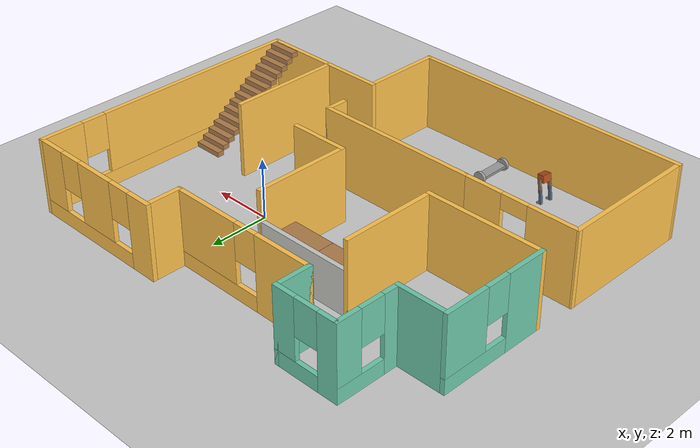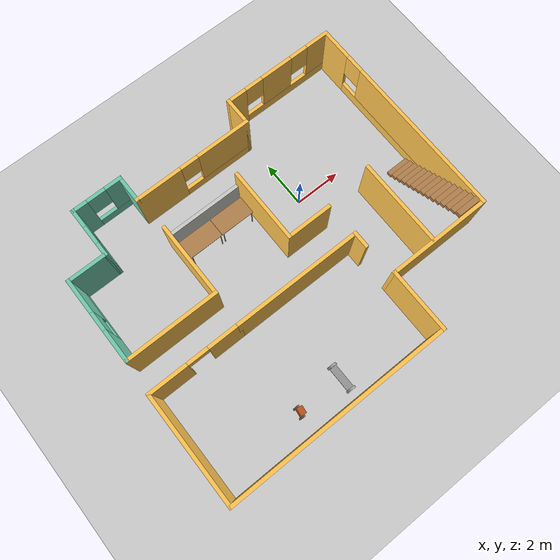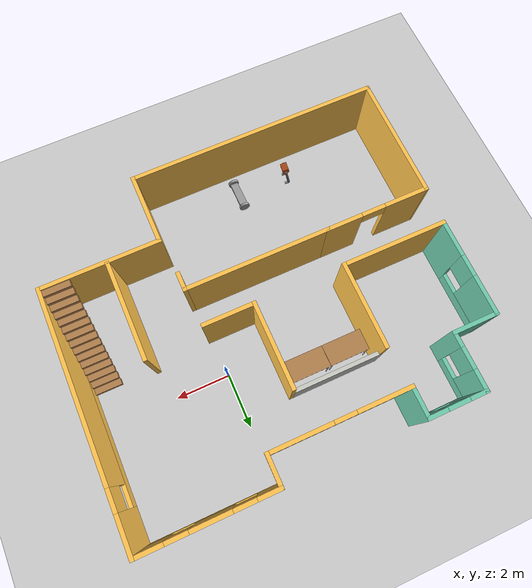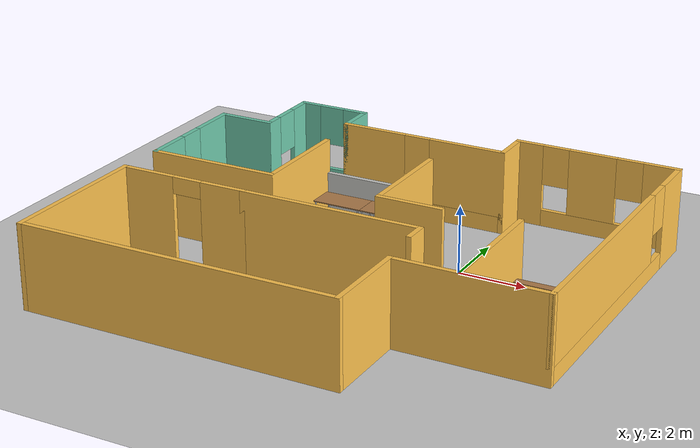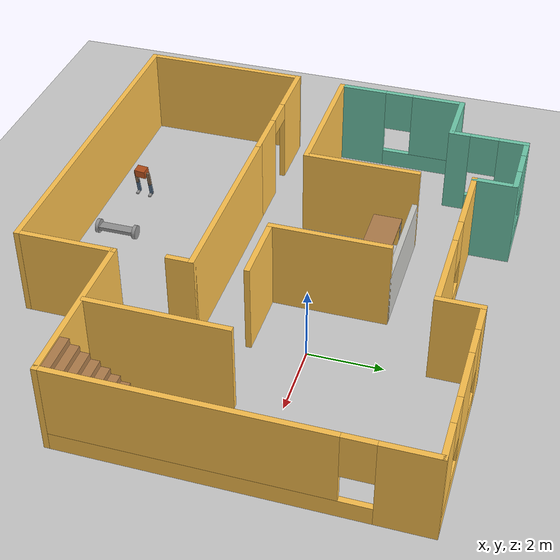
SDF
<sdf version="1.6">
 <world name="default">
  <plugin name="collision_map_creator" filename="libcollision_map_creator.so"/>
  <light name="sun" type="directional">
   <pose>0 0 10 0 -0 0</pose>
   <diffuse>0.8 0.8 0.8 1</diffuse>
   <specular>0.2 0.2 0.2 1</specular>
   <attenuation>
    <range>1000</range>
    <constant>0.9</constant>
    <linear>0.01</linear>
    <quadratic>0.001</quadratic>
   </attenuation>
   <direction>-0.5 0.1 -0.9</direction>
  </light>
  <model name="ground_plane">
   <static>1</static>
   <link name="link">
    <collision name="collision">
     <geometry><plane><normal>0 0 1</normal><size>100 100</size></plane></geometry>
     <surface><friction><ode><mu>100</mu><mu2>50</mu2></ode></friction></surface>
    </collision>
    <visual name="visual">
     <cast_shadows>0</cast_shadows>
     <geometry><plane><normal>0 0 1</normal><size>100 100</size></plane></geometry>
     <material>
      <script><uri>file://media/materials/scripts/gazebo.material</uri><name>Gazebo/Grey</name></script>
     </material>
    </visual>
   </link>
  </model>
  <gravity>0 0 -9.8</gravity>
  <magnetic_field>6e-06 2.3e-05 -4.2e-05</magnetic_field>
  <atmosphere type="adiabatic"/>
  <physics name="default_physics" default="0" type="ode">
   <max_step_size>0.001</max_step_size>
   <real_time_factor>1</real_time_factor>
   <real_time_update_rate>1000</real_time_update_rate>
  </physics>
  <scene><ambient>0.4 0.4 0.4 1</ambient><background>0.7 0.7 0.7 1</background><shadows>1</shadows></scene>
  <spherical_coordinates>
   <surface_model>EARTH_WGS84</surface_model>
   <latitude_deg>0</latitude_deg>
   <longitude_deg>0</longitude_deg>
   <elevation>0</elevation>
   <heading_deg>0</heading_deg>
  </spherical_coordinates>
  <model name="building">
   <pose>-2.14951 -1.63001 0 0 -0 0</pose>
   <link name="Stairs_0">
    <visual name="Stairs_0_Visual_0">
     <pose>6.28895 0.235116 0.083333 0 -0 0</pose>
     <geometry><box><size>1 0.233333 0.166667</size></box></geometry>
     <material>
      <script><uri>file://media/materials/scripts/gazebo.material</uri><name>Gazebo/Wood</name></script>
      <ambient>0.996078 0.47451 0.0196078 1</ambient>
     </material>
     <meta><layer>0</layer></meta>
    </visual>
    <collision name="Stairs_0_Collision_0">
     <geometry><box><size>1 0.233333 0.166667</size></box></geometry>
     <pose>6.28895 0.235116 0.083333 0 -0 0</pose>
    </collision>
    <visual name="Stairs_0_Visual_1">
     <pose>6.28895 0.001782 0.25 0 -0 0</pose>
     <geometry><box><size>1 0.233333 0.166667</size></box></geometry>
     <material>
      <script><uri>file://media/materials/scripts/gazebo.material</uri><name>Gazebo/Wood</name></script>
      <ambient>0.996078 0.47451 0.0196078 1</ambient>
     </material>
     <meta><layer>0</layer></meta>
    </visual>
    <collision name="Stairs_0_Collision_1">
     <geometry><box><size>1 0.233333 0.166667</size></box></geometry>
     <pose>6.28895 0.001782 0.25 0 -0 0</pose>
    </collision>
    <visual name="Stairs_0_Visual_2">
     <pose>6.28895 -0.231551 0.416667 0 -0 0</pose>
     <geometry><box><size>1 0.233333 0.166667</size></box></geometry>
     <material>
      <script><uri>file://media/materials/scripts/gazebo.material</uri><name>Gazebo/Wood</name></script>
      <ambient>0.996078 0.47451 0.0196078 1</ambient>
     </material>
     <meta><layer>0</layer></meta>
    </visual>
    <collision name="Stairs_0_Collision_2">
     <geometry><box><size>1 0.233333 0.166667</size></box></geometry>
     <pose>6.28895 -0.231551 0.416667 0 -0 0</pose>
    </collision>
    <visual name="Stairs_0_Visual_3">
     <pose>6.28895 -0.464884 0.583333 0 -0 0</pose>
     <geometry><box><size>1 0.233333 0.166667</size></box></geometry>
     <material>
      <script><uri>file://media/materials/scripts/gazebo.material</uri><name>Gazebo/Wood</name></script>
      <ambient>0.996078 0.47451 0.0196078 1</ambient>
     </material>
     <meta><layer>0</layer></meta>
    </visual>
    <collision name="Stairs_0_Collision_3">
     <geometry><box><size>1 0.233333 0.166667</size></box></geometry>
     <pose>6.28895 -0.464884 0.583333 0 -0 0</pose>
    </collision>
    <visual name="Stairs_0_Visual_4">
     <pose>6.28895 -0.698218 0.75 0 -0 0</pose>
     <geometry><box><size>1 0.233333 0.166667</size></box></geometry>
     <material>
      <script><uri>file://media/materials/scripts/gazebo.material</uri><name>Gazebo/Wood</name></script>
      <ambient>0.996078 0.47451 0.0196078 1</ambient>
     </material>
     <meta><layer>0</layer></meta>
    </visual>
    <collision name="Stairs_0_Collision_4">
     <geometry><box><size>1 0.233333 0.166667</size></box></geometry>
     <pose>6.28895 -0.698218 0.75 0 -0 0</pose>
    </collision>
    <visual name="Stairs_0_Visual_5">
     <pose>6.28895 -0.931551 0.916667 0 -0 0</pose>
     <geometry><box><size>1 0.233333 0.166667</size></box></geometry>
     <material>
      <script><uri>file://media/materials/scripts/gazebo.material</uri><name>Gazebo/Wood</name></script>
      <ambient>0.996078 0.47451 0.0196078 1</ambient>
     </material>
     <meta><layer>0</layer></meta>
    </visual>
    <collision name="Stairs_0_Collision_5">
     <geometry><box><size>1 0.233333 0.166667</size></box></geometry>
     <pose>6.28895 -0.931551 0.916667 0 -0 0</pose>
    </collision>
    <visual name="Stairs_0_Visual_6">
     <pose>6.28895 -1.16488 1.08333 0 -0 0</pose>
     <geometry><box><size>1 0.233333 0.166667</size></box></geometry>
     <material>
      <script><uri>file://media/materials/scripts/gazebo.material</uri><name>Gazebo/Wood</name></script>
      <ambient>0.996078 0.47451 0.0196078 1</ambient>
     </material>
     <meta><layer>0</layer></meta>
    </visual>
    <collision name="Stairs_0_Collision_6">
     <geometry><box><size>1 0.233333 0.166667</size></box></geometry>
     <pose>6.28895 -1.16488 1.08333 0 -0 0</pose>
    </collision>
    <visual name="Stairs_0_Visual_7">
     <pose>6.28895 -1.39822 1.25 0 -0 0</pose>
     <geometry><box><size>1 0.233333 0.166667</size></box></geometry>
     <material>
      <script><uri>file://media/materials/scripts/gazebo.material</uri><name>Gazebo/Wood</name></script>
      <ambient>0.996078 0.47451 0.0196078 1</ambient>
     </material>
     <meta><layer>0</layer></meta>
    </visual>
    <collision name="Stairs_0_Collision_7">
     <geometry><box><size>1 0.233333 0.166667</size></box></geometry>
     <pose>6.28895 -1.39822 1.25 0 -0 0</pose>
    </collision>
    <visual name="Stairs_0_Visual_8">
     <pose>6.28895 -1.63155 1.41667 0 -0 0</pose>
     <geometry><box><size>1 0.233333 0.166667</size></box></geometry>
     <material>
      <script><uri>file://media/materials/scripts/gazebo.material</uri><name>Gazebo/Wood</name></script>
      <ambient>0.996078 0.47451 0.0196078 1</ambient>
     </material>
     <meta><layer>0</layer></meta>
    </visual>
    <collision name="Stairs_0_Collision_8">
     <geometry><box><size>1 0.233333 0.166667</size></box></geometry>
     <pose>6.28895 -1.63155 1.41667 0 -0 0</pose>
    </collision>
    <visual name="Stairs_0_Visual_9">
     <pose>6.28895 -1.86488 1.58333 0 -0 0</pose>
     <geometry><box><size>1 0.233333 0.166667</size></box></geometry>
     <material>
      <script><uri>file://media/materials/scripts/gazebo.material</uri><name>Gazebo/Wood</name></script>
      <ambient>0.996078 0.47451 0.0196078 1</ambient>
     </material>
     <meta><layer>0</layer></meta>
    </visual>
    <collision name="Stairs_0_Collision_9">
     <geometry><box><size>1 0.233333 0.166667</size></box></geometry>
     <pose>6.28895 -1.86488 1.58333 0 -0 0</pose>
    </collision>
    <visual name="Stairs_0_Visual_10">
     <pose>6.28895 -2.09822 1.75 0 -0 0</pose>
     <geometry><box><size>1 0.233333 0.166667</size></box></geometry>
     <material>
      <script><uri>file://media/materials/scripts/gazebo.material</uri><name>Gazebo/Wood</name></script>
      <ambient>0.996078 0.47451 0.0196078 1</ambient>
     </material>
     <meta><layer>0</layer></meta>
    </visual>
    <collision name="Stairs_0_Collision_10">
     <geometry><box><size>1 0.233333 0.166667</size></box></geometry>
     <pose>6.28895 -2.09822 1.75 0 -0 0</pose>
    </collision>
    <visual name="Stairs_0_Visual_11">
     <pose>6.28895 -2.33155 1.91667 0 -0 0</pose>
     <geometry><box><size>1 0.233333 0.166667</size></box></geometry>
     <material>
      <script><uri>file://media/materials/scripts/gazebo.material</uri><name>Gazebo/Wood</name></script>
      <ambient>0.996078 0.47451 0.0196078 1</ambient>
     </material>
     <meta><layer>0</layer></meta>
    </visual>
    <collision name="Stairs_0_Collision_11">
     <geometry><box><size>1 0.233333 0.166667</size></box></geometry>
     <pose>6.28895 -2.33155 1.91667 0 -0 0</pose>
    </collision>
    <visual name="Stairs_0_Visual_12">
     <pose>6.28895 -2.56488 2.08333 0 -0 0</pose>
     <geometry><box><size>1 0.233333 0.166667</size></box></geometry>
     <material>
      <script><uri>file://media/materials/scripts/gazebo.material</uri><name>Gazebo/Wood</name></script>
      <ambient>0.996078 0.47451 0.0196078 1</ambient>
     </material>
     <meta><layer>0</layer></meta>
    </visual>
    <collision name="Stairs_0_Collision_12">
     <geometry><box><size>1 0.233333 0.166667</size></box></geometry>
     <pose>6.28895 -2.56488 2.08333 0 -0 0</pose>
    </collision>
    <visual name="Stairs_0_Visual_13">
     <pose>6.28895 -2.79822 2.25 0 -0 0</pose>
     <geometry><box><size>1 0.233333 0.166667</size></box></geometry>
     <material>
      <script><uri>file://media/materials/scripts/gazebo.material</uri><name>Gazebo/Wood</name></script>
      <ambient>0.996078 0.47451 0.0196078 1</ambient>
     </material>
     <meta><layer>0</layer></meta>
    </visual>
    <collision name="Stairs_0_Collision_13">
     <geometry><box><size>1 0.233333 0.166667</size></box></geometry>
     <pose>6.28895 -2.79822 2.25 0 -0 0</pose>
    </collision>
    <visual name="Stairs_0_Visual_14">
     <pose>6.28895 -3.03155 2.41667 0 -0 0</pose>
     <geometry><box><size>1 0.233333 0.166667</size></box></geometry>
     <material>
      <script><uri>file://media/materials/scripts/gazebo.material</uri><name>Gazebo/Wood</name></script>
      <ambient>0.996078 0.47451 0.0196078 1</ambient>
     </material>
     <meta><layer>0</layer></meta>
    </visual>
    <collision name="Stairs_0_Collision_14">
     <geometry><box><size>1 0.233333 0.166667</size></box></geometry>
     <pose>6.28895 -3.03155 2.41667 0 -0 0</pose>
    </collision>
   </link>
   <link name="Wall_11">
    <collision name="Wall_11_Collision">
     <geometry><box><size>1.75 0.15 2.5</size></box></geometry>
     <pose>0 0 1.25 0 -0 0</pose>
    </collision>
    <visual name="Wall_11_Visual">
     <pose>0 0 1.25 0 -0 0</pose>
     <geometry><box><size>1.75 0.15 2.5</size></box></geometry>
     <material>
      <script><uri>file://media/materials/scripts/gazebo.material</uri><name>Gazebo/Grey</name></script>
      <ambient>0.435294 0.796078 0.67451 1</ambient>
     </material>
     <meta><layer>0</layer></meta>
    </visual>
    <pose>-5.98549 3.75001 0 0 -0 0</pose>
   </link>
   <link name="Wall_12">
    <pose>-5.18549 4.80001 0 0 -0 1.5708</pose>
    <visual name="Wall_12_Visual_0">
     <pose>-0.822466 0 1.25 0 -0 0</pose>
     <geometry><box><size>0.605068 0.15 2.5</size></box></geometry>
     <material>
      <script><uri>file://media/materials/scripts/gazebo.material</uri><name>Gazebo/Grey</name></script>
      <ambient>0.435294 0.796078 0.67451 1</ambient>
     </material>
     <meta><layer>0</layer></meta>
    </visual>
    <collision name="Wall_12_Collision_0">
     <geometry><box><size>0.605068 0.15 2.5</size></box></geometry>
     <pose>-0.822466 0 1.25 0 -0 0</pose>
    </collision>
    <visual name="Wall_12_Visual_1">
     <pose>0.302534 0 0.25 0 -0 0</pose>
     <geometry><box><size>1.64493 0.15 0.5</size></box></geometry>
     <material>
      <script><uri>file://media/materials/scripts/gazebo.material</uri><name>Gazebo/Grey</name></script>
      <ambient>0.435294 0.796078 0.67451 1</ambient>
     </material>
     <meta><layer>0</layer></meta>
    </visual>
    <collision name="Wall_12_Collision_1">
     <geometry><box><size>1.64493 0.15 0.5</size></box></geometry>
     <pose>0.302534 0 0.25 0 -0 0</pose>
    </collision>
    <visual name="Wall_12_Visual_2">
     <pose>0.702534 0 1.5 0 -0 0</pose>
     <geometry><box><size>0.844932 0.15 2</size></box></geometry>
     <material>
      <script><uri>file://media/materials/scripts/gazebo.material</uri><name>Gazebo/Grey</name></script>
      <ambient>0.435294 0.796078 0.67451 1</ambient>
     </material>
     <meta><layer>0</layer></meta>
    </visual>
    <collision name="Wall_12_Collision_2">
     <geometry><box><size>0.844932 0.15 2</size></box></geometry>
     <pose>0.702534 0 1.5 0 -0 0</pose>
    </collision>
    <visual name="Wall_12_Visual_3">
     <pose>-0.119932 0 1.9 0 -0 0</pose>
     <geometry><box><size>0.8 0.15 1.2</size></box></geometry>
     <material>
      <script><uri>file://media/materials/scripts/gazebo.material</uri><name>Gazebo/Grey</name></script>
      <ambient>0.435294 0.796078 0.67451 1</ambient>
     </material>
     <meta><layer>0</layer></meta>
    </visual>
    <collision name="Wall_12_Collision_3">
     <geometry><box><size>0.8 0.15 1.2</size></box></geometry>
     <pose>-0.119932 0 1.9 0 -0 0</pose>
    </collision>
   </link>
   <link name="Wall_13">
    <pose>-4.13549 5.85001 0 0 -0 0</pose>
    <visual name="Wall_13_Visual_0">
     <pose>-0.782955 0 1.25 0 -0 0</pose>
     <geometry><box><size>0.684089 0.15 2.5</size></box></geometry>
     <material>
      <script><uri>file://media/materials/scripts/gazebo.material</uri><name>Gazebo/Grey</name></script>
      <ambient>0.435294 0.796078 0.67451 1</ambient>
     </material>
     <meta><layer>0</layer></meta>
    </visual>
    <collision name="Wall_13_Collision_0">
     <geometry><box><size>0.684089 0.15 2.5</size></box></geometry>
     <pose>-0.782955 0 1.25 0 -0 0</pose>
    </collision>
    <visual name="Wall_13_Visual_1">
     <pose>0.342045 0 0.25 0 -0 0</pose>
     <geometry><box><size>1.56591 0.15 0.5</size></box></geometry>
     <material>
      <script><uri>file://media/materials/scripts/gazebo.material</uri><name>Gazebo/Grey</name></script>
      <ambient>0.435294 0.796078 0.67451 1</ambient>
     </material>
     <meta><layer>0</layer></meta>
    </visual>
    <collision name="Wall_13_Collision_1">
     <geometry><box><size>1.56591 0.15 0.5</size></box></geometry>
     <pose>0.342045 0 0.25 0 -0 0</pose>
    </collision>
    <visual name="Wall_13_Visual_2">
     <pose>0.742045 0 1.5 0 -0 0</pose>
     <geometry><box><size>0.765911 0.15 2</size></box></geometry>
     <material>
      <script><uri>file://media/materials/scripts/gazebo.material</uri><name>Gazebo/Grey</name></script>
      <ambient>0.435294 0.796078 0.67451 1</ambient>
     </material>
     <meta><layer>0</layer></meta>
    </visual>
    <collision name="Wall_13_Collision_2">
     <geometry><box><size>0.765911 0.15 2</size></box></geometry>
     <pose>0.742045 0 1.5 0 -0 0</pose>
    </collision>
    <visual name="Wall_13_Visual_3">
     <pose>-0.040911 0 1.9 0 -0 0</pose>
     <geometry><box><size>0.8 0.15 1.2</size></box></geometry>
     <material>
      <script><uri>file://media/materials/scripts/gazebo.material</uri><name>Gazebo/Grey</name></script>
      <ambient>0.435294 0.796078 0.67451 1</ambient>
     </material>
     <meta><layer>0</layer></meta>
    </visual>
    <collision name="Wall_13_Collision_3">
     <geometry><box><size>0.8 0.15 1.2</size></box></geometry>
     <pose>-0.040911 0 1.9 0 -0 0</pose>
    </collision>
   </link>
   <link name="Wall_14">
    <collision name="Wall_14_Collision">
     <geometry><box><size>1.25 0.15 2.5</size></box></geometry>
     <pose>0 0 1.25 0 -0 0</pose>
    </collision>
    <visual name="Wall_14_Visual">
     <pose>0 0 1.25 0 -0 0</pose>
     <geometry><box><size>1.25 0.15 2.5</size></box></geometry>
     <material>
      <script><uri>file://media/materials/scripts/gazebo.material</uri><name>Gazebo/Grey</name></script>
      <ambient>0.435294 0.796078 0.67451 1</ambient>
     </material>
     <meta><layer>0</layer></meta>
    </visual>
    <pose>-3.08549 5.30001 0 0 0 -1.5708</pose>
   </link>
   <link name="Wall_15">
    <pose>-0.535492 4.75001 0 0 -0 0</pose>
    <visual name="Wall_15_Visual_0">
     <pose>-1.59834 0 1.25 0 -0 0</pose>
     <geometry><box><size>2.05332 0.15 2.5</size></box></geometry>
     <material>
      <script><uri>file://media/materials/scripts/gazebo.material</uri><name>Gazebo/Grey</name></script>
      <ambient>1 0.764706 0.305882 1</ambient>
     </material>
     <meta><layer>0</layer></meta>
    </visual>
    <collision name="Wall_15_Collision_0">
     <geometry><box><size>2.05332 0.15 2.5</size></box></geometry>
     <pose>-1.59834 0 1.25 0 -0 0</pose>
    </collision>
    <visual name="Wall_15_Visual_1">
     <pose>1.02666 0 0.25 0 -0 0</pose>
     <geometry><box><size>3.19668 0.15 0.5</size></box></geometry>
     <material>
      <script><uri>file://media/materials/scripts/gazebo.material</uri><name>Gazebo/Grey</name></script>
      <ambient>1 0.764706 0.305882 1</ambient>
     </material>
     <meta><layer>0</layer></meta>
    </visual>
    <collision name="Wall_15_Collision_1">
     <geometry><box><size>3.19668 0.15 0.5</size></box></geometry>
     <pose>1.02666 0 0.25 0 -0 0</pose>
    </collision>
    <visual name="Wall_15_Visual_2">
     <pose>1.42666 0 1.5 0 -0 0</pose>
     <geometry><box><size>2.39668 0.15 2</size></box></geometry>
     <material>
      <script><uri>file://media/materials/scripts/gazebo.material</uri><name>Gazebo/Grey</name></script>
      <ambient>1 0.764706 0.305882 1</ambient>
     </material>
     <meta><layer>0</layer></meta>
    </visual>
    <collision name="Wall_15_Collision_2">
     <geometry><box><size>2.39668 0.15 2</size></box></geometry>
     <pose>1.42666 0 1.5 0 -0 0</pose>
    </collision>
    <visual name="Wall_15_Visual_3">
     <pose>-0.171681 0 1.9 0 -0 0</pose>
     <geometry><box><size>0.8 0.15 1.2</size></box></geometry>
     <material>
      <script><uri>file://media/materials/scripts/gazebo.material</uri><name>Gazebo/Grey</name></script>
      <ambient>1 0.764706 0.305882 1</ambient>
     </material>
     <meta><layer>0</layer></meta>
    </visual>
    <collision name="Wall_15_Collision_3">
     <geometry><box><size>0.8 0.15 1.2</size></box></geometry>
     <pose>-0.171681 0 1.9 0 -0 0</pose>
    </collision>
   </link>
   <link name="Wall_16">
    <collision name="Wall_16_Collision">
     <geometry><box><size>1.25 0.15 2.5</size></box></geometry>
     <pose>0 0 1.25 0 -0 0</pose>
    </collision>
    <visual name="Wall_16_Visual">
     <pose>0 0 1.25 0 -0 0</pose>
     <geometry><box><size>1.25 0.15 2.5</size></box></geometry>
     <material>
      <script><uri>file://media/materials/scripts/gazebo.material</uri><name>Gazebo/Grey</name></script>
      <ambient>1 0.764706 0.305882 1</ambient>
     </material>
     <meta><layer>0</layer></meta>
    </visual>
    <pose>2.01451 5.30001 0 0 -0 1.5708</pose>
   </link>
   <link name="Wall_17">
    <pose>4.43951 5.85001 0 0 -0 0</pose>
    <visual name="Wall_17_Visual_0">
     <pose>-2.05936 0 1.25 0 -0 0</pose>
     <geometry><box><size>0.881289 0.15 2.5</size></box></geometry>
     <material>
      <script><uri>file://media/materials/scripts/gazebo.material</uri><name>Gazebo/Grey</name></script>
      <ambient>1 0.764706 0.305882 1</ambient>
     </material>
     <meta><layer>0</layer></meta>
    </visual>
    <collision name="Wall_17_Collision_0">
     <geometry><box><size>0.881289 0.15 2.5</size></box></geometry>
     <pose>-2.05936 0 1.25 0 -0 0</pose>
    </collision>
    <visual name="Wall_17_Visual_1">
     <pose>0.440644 0 0.25 0 -0 0</pose>
     <geometry><box><size>4.11871 0.15 0.5</size></box></geometry>
     <material>
      <script><uri>file://media/materials/scripts/gazebo.material</uri><name>Gazebo/Grey</name></script>
      <ambient>1 0.764706 0.305882 1</ambient>
     </material>
     <meta><layer>0</layer></meta>
    </visual>
    <collision name="Wall_17_Collision_1">
     <geometry><box><size>4.11871 0.15 0.5</size></box></geometry>
     <pose>0.440644 0 0.25 0 -0 0</pose>
    </collision>
    <visual name="Wall_17_Visual_2">
     <pose>-0.10053 0 1.5 0 -0 0</pose>
     <geometry><box><size>1.43636 0.15 2</size></box></geometry>
     <material>
      <script><uri>file://media/materials/scripts/gazebo.material</uri><name>Gazebo/Grey</name></script>
      <ambient>1 0.764706 0.305882 1</ambient>
     </material>
     <meta><layer>0</layer></meta>
    </visual>
    <collision name="Wall_17_Collision_2">
     <geometry><box><size>1.43636 0.15 2</size></box></geometry>
     <pose>-0.10053 0 1.5 0 -0 0</pose>
    </collision>
    <visual name="Wall_17_Visual_3">
     <pose>1.95883 0 1.5 0 -0 0</pose>
     <geometry><box><size>1.08235 0.15 2</size></box></geometry>
     <material>
      <script><uri>file://media/materials/scripts/gazebo.material</uri><name>Gazebo/Grey</name></script>
      <ambient>1 0.764706 0.305882 1</ambient>
     </material>
     <meta><layer>0</layer></meta>
    </visual>
    <collision name="Wall_17_Collision_3">
     <geometry><box><size>1.08235 0.15 2</size></box></geometry>
     <pose>1.95883 0 1.5 0 -0 0</pose>
    </collision>
    <visual name="Wall_17_Visual_4">
     <pose>-1.21871 0 1.9 0 -0 0</pose>
     <geometry><box><size>0.8 0.15 1.2</size></box></geometry>
     <material>
      <script><uri>file://media/materials/scripts/gazebo.material</uri><name>Gazebo/Grey</name></script>
      <ambient>1 0.764706 0.305882 1</ambient>
     </material>
     <meta><layer>0</layer></meta>
    </visual>
    <collision name="Wall_17_Collision_4">
     <geometry><box><size>0.8 0.15 1.2</size></box></geometry>
     <pose>-1.21871 0 1.9 0 -0 0</pose>
    </collision>
    <visual name="Wall_17_Visual_5">
     <pose>1.01765 0 1.9 0 -0 0</pose>
     <geometry><box><size>0.8 0.15 1.2</size></box></geometry>
     <material>
      <script><uri>file://media/materials/scripts/gazebo.material</uri><name>Gazebo/Grey</name></script>
      <ambient>1 0.764706 0.305882 1</ambient>
     </material>
     <meta><layer>0</layer></meta>
    </visual>
    <collision name="Wall_17_Collision_5">
     <geometry><box><size>0.8 0.15 1.2</size></box></geometry>
     <pose>1.01765 0 1.9 0 -0 0</pose>
    </collision>
   </link>
   <link name="Wall_18">
    <pose>6.86451 1.30001 0 0 0 -1.5708</pose>
    <visual name="Wall_18_Visual_0">
     <pose>-3.90149 0 1.25 0 -0 0</pose>
     <geometry><box><size>1.44703 0.15 2.5</size></box></geometry>
     <material>
      <script><uri>file://media/materials/scripts/gazebo.material</uri><name>Gazebo/Grey</name></script>
      <ambient>1 0.764706 0.305882 1</ambient>
     </material>
     <meta><layer>0</layer></meta>
    </visual>
    <collision name="Wall_18_Collision_0">
     <geometry><box><size>1.44703 0.15 2.5</size></box></geometry>
     <pose>-3.90149 0 1.25 0 -0 0</pose>
    </collision>
    <visual name="Wall_18_Visual_1">
     <pose>0.723515 0 0.25 0 -0 0</pose>
     <geometry><box><size>7.80297 0.15 0.5</size></box></geometry>
     <material>
      <script><uri>file://media/materials/scripts/gazebo.material</uri><name>Gazebo/Grey</name></script>
      <ambient>1 0.764706 0.305882 1</ambient>
     </material>
     <meta><layer>0</layer></meta>
    </visual>
    <collision name="Wall_18_Collision_1">
     <geometry><box><size>7.80297 0.15 0.5</size></box></geometry>
     <pose>0.723515 0 0.25 0 -0 0</pose>
    </collision>
    <visual name="Wall_18_Visual_2">
     <pose>1.12352 0 1.5 0 -0 0</pose>
     <geometry><box><size>7.00297 0.15 2</size></box></geometry>
     <material>
      <script><uri>file://media/materials/scripts/gazebo.material</uri><name>Gazebo/Grey</name></script>
      <ambient>1 0.764706 0.305882 1</ambient>
     </material>
     <meta><layer>0</layer></meta>
    </visual>
    <collision name="Wall_18_Collision_2">
     <geometry><box><size>7.00297 0.15 2</size></box></geometry>
     <pose>1.12352 0 1.5 0 -0 0</pose>
    </collision>
    <visual name="Wall_18_Visual_3">
     <pose>-2.77797 0 1.9 0 -0 0</pose>
     <geometry><box><size>0.8 0.15 1.2</size></box></geometry>
     <material>
      <script><uri>file://media/materials/scripts/gazebo.material</uri><name>Gazebo/Grey</name></script>
      <ambient>1 0.764706 0.305882 1</ambient>
     </material>
     <meta><layer>0</layer></meta>
    </visual>
    <collision name="Wall_18_Collision_3">
     <geometry><box><size>0.8 0.15 1.2</size></box></geometry>
     <pose>-2.77797 0 1.9 0 -0 0</pose>
    </collision>
   </link>
   <link name="Wall_19">
    <collision name="Wall_19_Collision">
     <geometry><box><size>4.5 0.15 2.5</size></box></geometry>
     <pose>0 0 1.25 0 -0 0</pose>
    </collision>
    <visual name="Wall_19_Visual">
     <pose>0 0 1.25 0 -0 0</pose>
     <geometry><box><size>4.5 0.15 2.5</size></box></geometry>
     <material>
      <script><uri>file://media/materials/scripts/gazebo.material</uri><name>Gazebo/Grey</name></script>
      <ambient>1 0.764706 0.305882 1</ambient>
     </material>
     <meta><layer>0</layer></meta>
    </visual>
    <pose>4.68951 -3.24999 0 0 -0 3.14159</pose>
   </link>
   <link name="Wall_20">
    <collision name="Wall_20_Collision">
     <geometry><box><size>2.75 0.15 2.5</size></box></geometry>
     <pose>0 0 1.25 0 -0 0</pose>
    </collision>
    <visual name="Wall_20_Visual">
     <pose>0 0 1.25 0 -0 0</pose>
     <geometry><box><size>2.75 0.15 2.5</size></box></geometry>
     <material>
      <script><uri>file://media/materials/scripts/gazebo.material</uri><name>Gazebo/Grey</name></script>
      <ambient>1 0.764706 0.305882 1</ambient>
     </material>
     <meta><layer>0</layer></meta>
    </visual>
    <pose>2.51451 -4.54999 0 0 0 -1.5708</pose>
   </link>
   <link name="Wall_21">
    <collision name="Wall_21_Collision">
     <geometry><box><size>9.529 0.15 2.5</size></box></geometry>
     <pose>0 0 1.25 0 -0 0</pose>
    </collision>
    <visual name="Wall_21_Visual">
     <pose>0 0 1.25 0 -0 0</pose>
     <geometry><box><size>9.529 0.15 2.5</size></box></geometry>
     <material>
      <script><uri>file://media/materials/scripts/gazebo.material</uri><name>Gazebo/Grey</name></script>
      <ambient>1 0.764706 0.305882 1</ambient>
     </material>
     <meta><layer>0</layer></meta>
    </visual>
    <pose>-2.17499 -5.84999 0 0 -0 3.14159</pose>
   </link>
   <link name="Wall_22">
    <collision name="Wall_22_Collision">
     <geometry><box><size>4.75 0.15 2.5</size></box></geometry>
     <pose>0 0 1.25 0 -0 0</pose>
    </collision>
    <visual name="Wall_22_Visual">
     <pose>0 0 1.25 0 -0 0</pose>
     <geometry><box><size>4.75 0.15 2.5</size></box></geometry>
     <material>
      <script><uri>file://media/materials/scripts/gazebo.material</uri><name>Gazebo/Grey</name></script>
      <ambient>1 0.764706 0.305882 1</ambient>
     </material>
     <meta><layer>0</layer></meta>
    </visual>
    <pose>-6.86399 -3.54999 0 0 -0 1.57058</pose>
   </link>
   <link name="Wall_24">
    <collision name="Wall_24_Collision">
     <geometry><box><size>4 0.15 2.5</size></box></geometry>
     <pose>0 0 1.25 0 -0 0</pose>
    </collision>
    <visual name="Wall_24_Visual">
     <pose>0 0 1.25 0 -0 0</pose>
     <geometry><box><size>4 0.15 2.5</size></box></geometry>
     <material>
      <script><uri>file://media/materials/scripts/gazebo.material</uri><name>Gazebo/Grey</name></script>
      <ambient>1 0.764706 0.305882 1</ambient>
     </material>
     <meta><layer>0</layer></meta>
    </visual>
    <pose>-4.86049 0.150008 0 0 -0 0</pose>
   </link>
   <link name="Wall_27">
    <collision name="Wall_27_Collision">
     <geometry><box><size>3.25 0.15 2.5</size></box></geometry>
     <pose>0 0 1.25 0 -0 0</pose>
    </collision>
    <visual name="Wall_27_Visual">
     <pose>0 0 1.25 0 -0 0</pose>
     <geometry><box><size>3.25 0.15 2.5</size></box></geometry>
     <material>
      <script><uri>file://media/materials/scripts/gazebo.material</uri><name>Gazebo/Grey</name></script>
      <ambient>1 0.764706 0.305882 1</ambient>
     </material>
     <meta><layer>0</layer></meta>
    </visual>
    <pose>-2.93549 1.70001 0 0 -0 1.5708</pose>
   </link>
   <link name="Wall_28">
    <collision name="Wall_28_Collision">
     <geometry><box><size>3.5 0.15 1.5</size></box></geometry>
     <pose>0 0 0.75 0 -0 0</pose>
    </collision>
    <visual name="Wall_28_Visual">
     <pose>0 0 0.75 0 -0 0</pose>
     <geometry><box><size>3.5 0.15 1.5</size></box></geometry>
     <material>
      <script><uri>file://media/materials/scripts/gazebo.material</uri><name>Gazebo/CeilingTiled</name></script>
      <ambient>1 0.764706 0.305882 1</ambient>
     </material>
     <meta><layer>0</layer></meta>
    </visual>
    <pose>-1.26049 3.25001 0 0 -0 0</pose>
   </link>
   <link name="Wall_31">
    <pose>-4.92449 -1.24999 0 0 -0 0</pose>
    <visual name="Wall_31_Visual_0">
     <pose>-1.15892 0 1.25 0 -0 0</pose>
     <geometry><box><size>1.71048 0.15 2.5</size></box></geometry>
     <material>
      <script><uri>file://media/materials/scripts/gazebo.material</uri><name>Gazebo/Grey</name></script>
      <ambient>1 0.764706 0.305882 1</ambient>
     </material>
     <meta><layer>0</layer></meta>
    </visual>
    <collision name="Wall_31_Collision_0">
     <geometry><box><size>1.71048 0.15 2.5</size></box></geometry>
     <pose>-1.15892 0 1.25 0 -0 0</pose>
    </collision>
    <visual name="Wall_31_Visual_1">
     <pose>1.30524 0 1.25 0 -0 0</pose>
     <geometry><box><size>1.41785 0.15 2.5</size></box></geometry>
     <material>
      <script><uri>file://media/materials/scripts/gazebo.material</uri><name>Gazebo/Grey</name></script>
      <ambient>1 0.764706 0.305882 1</ambient>
     </material>
     <meta><layer>0</layer></meta>
    </visual>
    <collision name="Wall_31_Collision_1">
     <geometry><box><size>1.41785 0.15 2.5</size></box></geometry>
     <pose>1.30524 0 1.25 0 -0 0</pose>
    </collision>
    <visual name="Wall_31_Visual_2">
     <pose>0.146316 0 2.25 0 -0 0</pose>
     <geometry><box><size>0.9 0.15 0.5</size></box></geometry>
     <material>
      <script><uri>file://media/materials/scripts/gazebo.material</uri><name>Gazebo/Grey</name></script>
      <ambient>1 0.764706 0.305882 1</ambient>
     </material>
     <meta><layer>0</layer></meta>
    </visual>
    <collision name="Wall_31_Collision_2">
     <geometry><box><size>0.9 0.15 0.5</size></box></geometry>
     <pose>0.146316 0 2.25 0 -0 0</pose>
    </collision>
   </link>
   <link name="Wall_32">
    <collision name="Wall_32_Collision">
     <geometry><box><size>5.5 0.15 2.5</size></box></geometry>
     <pose>0 0 1.25 0 -0 0</pose>
    </collision>
    <visual name="Wall_32_Visual">
     <pose>0 0 1.25 0 -0 0</pose>
     <geometry><box><size>5.5 0.15 2.5</size></box></geometry>
     <material>
      <script><uri>file://media/materials/scripts/gazebo.material</uri><name>Gazebo/Grey</name></script>
      <ambient>1 0.764706 0.305882 1</ambient>
     </material>
     <meta><layer>0</layer></meta>
    </visual>
    <pose>-0.310493 -1.24999 0 0 -0 0</pose>
   </link>
   <link name="Wall_33">
    <collision name="Wall_33_Collision">
     <geometry><box><size>0.75 0.15 2.5</size></box></geometry>
     <pose>0 0 1.25 0 -0 0</pose>
    </collision>
    <visual name="Wall_33_Visual">
     <pose>0 0 1.25 0 -0 0</pose>
     <geometry><box><size>0.75 0.15 2.5</size></box></geometry>
     <material>
      <script><uri>file://media/materials/scripts/gazebo.material</uri><name>Gazebo/Grey</name></script>
      <ambient>1 0.764706 0.305882 1</ambient>
     </material>
     <meta><layer>0</layer></meta>
    </visual>
    <pose>2.36451 -1.54999 0 0 0 -1.5708</pose>
   </link>
   <link name="Wall_40">
    <collision name="Wall_40_Collision">
     <geometry><box><size>3.75 0.15 2.5</size></box></geometry>
     <pose>0 0 1.25 0 -0 0</pose>
    </collision>
    <visual name="Wall_40_Visual">
     <pose>0 0 1.25 0 -0 0</pose>
     <geometry><box><size>3.75 0.15 2.5</size></box></geometry>
     <material>
      <script><uri>file://media/materials/scripts/gazebo.material</uri><name>Gazebo/Grey</name></script>
      <ambient>1 0.764706 0.305882 1</ambient>
     </material>
     <meta><layer>0</layer></meta>
    </visual>
    <pose>4.42532 -1.37584 0 0 -0 1.5708</pose>
   </link>
   <link name="Wall_43">
    <collision name="Wall_43_Collision">
     <geometry><box><size>3.25 0.15 2.5</size></box></geometry>
     <pose>0 0 1.25 0 -0 0</pose>
    </collision>
    <visual name="Wall_43_Visual">
     <pose>0 0 1.25 0 -0 0</pose>
     <geometry><box><size>3.25 0.15 2.5</size></box></geometry>
     <material>
      <script><uri>file://media/materials/scripts/gazebo.material</uri><name>Gazebo/Grey</name></script>
      <ambient>1 0.764706 0.305882 1</ambient>
     </material>
     <meta><layer>0</layer></meta>
    </visual>
    <pose>0.414508 1.70001 0 0 0 -1.5708</pose>
   </link>
   <link name="Wall_44">
    <collision name="Wall_44_Collision">
     <geometry><box><size>2 0.15 2.5</size></box></geometry>
     <pose>0 0 1.25 0 -0 0</pose>
    </collision>
    <visual name="Wall_44_Visual">
     <pose>0 0 1.25 0 -0 0</pose>
     <geometry><box><size>2 0.15 2.5</size></box></geometry>
     <material>
      <script><uri>file://media/materials/scripts/gazebo.material</uri><name>Gazebo/Grey</name></script>
      <ambient>1 0.764706 0.305882 1</ambient>
     </material>
     <meta><layer>0</layer></meta>
    </visual>
    <pose>1.33951 0.150008 0 0 -0 0</pose>
   </link>
   <link name="Wall_9">
    <pose>-6.78549 1.95001 0 0 -0 1.5708</pose>
    <visual name="Wall_9_Visual_0">
     <pose>-1.16301 0 1.25 0 -0 0</pose>
     <geometry><box><size>1.42397 0.15 2.5</size></box></geometry>
     <material>
      <script><uri>file://media/materials/scripts/gazebo.material</uri><name>Gazebo/Grey</name></script>
      <ambient>0.435294 0.796078 0.67451 1</ambient>
     </material>
     <meta><layer>0</layer></meta>
    </visual>
    <collision name="Wall_9_Collision_0">
     <geometry><box><size>1.42397 0.15 2.5</size></box></geometry>
     <pose>-1.16301 0 1.25 0 -0 0</pose>
    </collision>
    <visual name="Wall_9_Visual_1">
     <pose>0.711987 0 0.25 0 -0 0</pose>
     <geometry><box><size>2.32603 0.15 0.5</size></box></geometry>
     <material>
      <script><uri>file://media/materials/scripts/gazebo.material</uri><name>Gazebo/Grey</name></script>
      <ambient>0.435294 0.796078 0.67451 1</ambient>
     </material>
     <meta><layer>0</layer></meta>
    </visual>
    <collision name="Wall_9_Collision_1">
     <geometry><box><size>2.32603 0.15 0.5</size></box></geometry>
     <pose>0.711987 0 0.25 0 -0 0</pose>
    </collision>
    <visual name="Wall_9_Visual_2">
     <pose>1.11199 0 1.5 0 -0 0</pose>
     <geometry><box><size>1.52603 0.15 2</size></box></geometry>
     <material>
      <script><uri>file://media/materials/scripts/gazebo.material</uri><name>Gazebo/Grey</name></script>
      <ambient>0.435294 0.796078 0.67451 1</ambient>
     </material>
     <meta><layer>0</layer></meta>
    </visual>
    <collision name="Wall_9_Collision_2">
     <geometry><box><size>1.52603 0.15 2</size></box></geometry>
     <pose>1.11199 0 1.5 0 -0 0</pose>
    </collision>
    <visual name="Wall_9_Visual_3">
     <pose>-0.051026 0 1.9 0 -0 0</pose>
     <geometry><box><size>0.8 0.15 1.2</size></box></geometry>
     <material>
      <script><uri>file://media/materials/scripts/gazebo.material</uri><name>Gazebo/Grey</name></script>
      <ambient>0.435294 0.796078 0.67451 1</ambient>
     </material>
     <meta><layer>0</layer></meta>
    </visual>
    <collision name="Wall_9_Collision_3">
     <geometry><box><size>0.8 0.15 1.2</size></box></geometry>
     <pose>-0.051026 0 1.9 0 -0 0</pose>
    </collision>
   </link>
   <static>1</static>
  </model>
  <model name="table">
   <static>1</static>
   <link name="link">
    <collision name="surface">
     <pose>0 0 1 0 -0 0</pose>
     <geometry><box><size>1.5 0.8 0.03</size></box></geometry>
     <surface><friction><ode><mu>0.6</mu><mu2>0.6</mu2></ode></friction></surface>
    </collision>
    <visual name="visual1">
     <pose>0 0 1 0 -0 0</pose>
     <geometry><box><size>1.5 0.8 0.03</size></box></geometry>
     <material>
      <script><uri>file://media/materials/scripts/gazebo.material</uri><name>Gazebo/Wood</name></script>
     </material>
    </visual>
    <collision name="front_left_leg">
     <pose>0.68 0.38 0.5 0 -0 0</pose>
     <geometry><cylinder><radius>0.02</radius><length>1</length></cylinder></geometry>
    </collision>
    <visual name="front_left_leg">
     <pose>0.68 0.38 0.5 0 -0 0</pose>
     <geometry><cylinder><radius>0.02</radius><length>1</length></cylinder></geometry>
     <material>
      <script><uri>file://media/materials/scripts/gazebo.material</uri><name>Gazebo/Grey</name></script>
     </material>
    </visual>
    <collision name="front_right_leg">
     <pose>0.68 -0.38 0.5 0 -0 0</pose>
     <geometry><cylinder><radius>0.02</radius><length>1</length></cylinder></geometry>
    </collision>
    <visual name="front_right_leg">
     <pose>0.68 -0.38 0.5 0 -0 0</pose>
     <geometry><cylinder><radius>0.02</radius><length>1</length></cylinder></geometry>
     <material>
      <script><uri>file://media/materials/scripts/gazebo.material</uri><name>Gazebo/Grey</name></script>
     </material>
    </visual>
    <collision name="back_right_leg">
     <pose>-0.68 -0.38 0.5 0 -0 0</pose>
     <geometry><cylinder><radius>0.02</radius><length>1</length></cylinder></geometry>
    </collision>
    <visual name="back_right_leg">
     <pose>-0.68 -0.38 0.5 0 -0 0</pose>
     <geometry><cylinder><radius>0.02</radius><length>1</length></cylinder></geometry>
     <material>
      <script><uri>file://media/materials/scripts/gazebo.material</uri><name>Gazebo/Grey</name></script>
     </material>
    </visual>
    <collision name="back_left_leg">
     <pose>-0.68 0.38 0.5 0 -0 0</pose>
     <geometry><cylinder><radius>0.02</radius><length>1</length></cylinder></geometry>
    </collision>
    <visual name="back_left_leg">
     <pose>-0.68 0.38 0.5 0 -0 0</pose>
     <geometry><cylinder><radius>0.02</radius><length>1</length></cylinder></geometry>
     <material>
      <script><uri>file://media/materials/scripts/gazebo.material</uri><name>Gazebo/Grey</name></script>
     </material>
    </visual>
   </link>
   <pose>-4.16325 0.916936 0 0 -0 0</pose>
  </model>
  <model name="table_0">
   <static>1</static>
   <link name="link">
    <collision name="surface">
     <pose>0 0 1 0 -0 0</pose>
     <geometry><box><size>1.5 0.8 0.03</size></box></geometry>
     <surface><friction><ode><mu>0.6</mu><mu2>0.6</mu2></ode></friction></surface>
    </collision>
    <visual name="visual1">
     <pose>0 0 1 0 -0 0</pose>
     <geometry><box><size>1.5 0.8 0.03</size></box></geometry>
     <material>
      <script><uri>file://media/materials/scripts/gazebo.material</uri><name>Gazebo/Wood</name></script>
     </material>
    </visual>
    <collision name="front_left_leg">
     <pose>0.68 0.38 0.5 0 -0 0</pose>
     <geometry><cylinder><radius>0.02</radius><length>1</length></cylinder></geometry>
    </collision>
    <visual name="front_left_leg">
     <pose>0.68 0.38 0.5 0 -0 0</pose>
     <geometry><cylinder><radius>0.02</radius><length>1</length></cylinder></geometry>
     <material>
      <script><uri>file://media/materials/scripts/gazebo.material</uri><name>Gazebo/Grey</name></script>
     </material>
    </visual>
    <collision name="front_right_leg">
     <pose>0.68 -0.38 0.5 0 -0 0</pose>
     <geometry><cylinder><radius>0.02</radius><length>1</length></cylinder></geometry>
    </collision>
    <visual name="front_right_leg">
     <pose>0.68 -0.38 0.5 0 -0 0</pose>
     <geometry><cylinder><radius>0.02</radius><length>1</length></cylinder></geometry>
     <material>
      <script><uri>file://media/materials/scripts/gazebo.material</uri><name>Gazebo/Grey</name></script>
     </material>
    </visual>
    <collision name="back_right_leg">
     <pose>-0.68 -0.38 0.5 0 -0 0</pose>
     <geometry><cylinder><radius>0.02</radius><length>1</length></cylinder></geometry>
    </collision>
    <visual name="back_right_leg">
     <pose>-0.68 -0.38 0.5 0 -0 0</pose>
     <geometry><cylinder><radius>0.02</radius><length>1</length></cylinder></geometry>
     <material>
      <script><uri>file://media/materials/scripts/gazebo.material</uri><name>Gazebo/Grey</name></script>
     </material>
    </visual>
    <collision name="back_left_leg">
     <pose>-0.68 0.38 0.5 0 -0 0</pose>
     <geometry><cylinder><radius>0.02</radius><length>1</length></cylinder></geometry>
    </collision>
    <visual name="back_left_leg">
     <pose>-0.68 0.38 0.5 0 -0 0</pose>
     <geometry><cylinder><radius>0.02</radius><length>1</length></cylinder></geometry>
     <material>
      <script><uri>file://media/materials/scripts/gazebo.material</uri><name>Gazebo/Grey</name></script>
     </material>
    </visual>
   </link>
   <pose>-2.65868 0.916299 0 0 -0 0</pose>
  </model>
  <model name="humanoid">
   <link name="link_0">
    <pose>0.043928 -0.199999 -0.333571 0 -0 0</pose>
    <inertial>
     <mass>1</mass>
     <inertia>
      <ixx>0.166667</ixx>
      <ixy>0</ixy>
      <ixz>0</ixz>
      <iyy>0.166667</iyy>
      <iyz>0</iyz>
      <izz>0.166667</izz>
     </inertia>
    </inertial>
    <visual name="visual">
     <geometry><box><size>0.2 0.08 0.05</size></box></geometry>
     <material>
      <lighting>1</lighting>
      <script><uri>file://media/materials/scripts/gazebo.material</uri><name>Gazebo/Grey</name></script>
      <ambient>0.3 0.3 0.3 1</ambient>
      <diffuse>0.7 0.7 0.7 1</diffuse>
      <specular>0.01 0.01 0.01 1</specular>
      <emissive>0 0 0 1</emissive>
      <shader type="vertex"><normal_map>__default__</normal_map></shader>
     </material>
    </visual>
    <collision name="collision">
     <geometry><box><size>0.2 0.08 0.05</size></box></geometry>
     <surface>
      <friction>
       <ode><mu>1</mu><mu2>1</mu2><fdir1>0 0 0</fdir1><slip1>0</slip1><slip2>0</slip2></ode>
       <torsional>
        <coefficient>1</coefficient>
        <patch_radius>0</patch_radius>
        <surface_radius>0</surface_radius>
        <use_patch_radius>1</use_patch_radius>
        <ode><slip>0</slip></ode>
       </torsional>
      </friction>
      <bounce><restitution_coefficient>0</restitution_coefficient><threshold>1e+06</threshold></bounce>
      <contact>
       <collide_without_contact>0</collide_without_contact>
       <collide_without_contact_bitmask>1</collide_without_contact_bitmask>
       <collide_bitmask>1</collide_bitmask>
       <ode>
        <soft_cfm>0</soft_cfm>
        <soft_erp>0.2</soft_erp>
        <kp>1e+13</kp>
        <kd>1</kd>
        <max_vel>0.01</max_vel>
        <min_depth>0</min_depth>
       </ode>
       <bullet>
        <split_impulse>1</split_impulse>
        <split_impulse_penetration_threshold>-0.01</split_impulse_penetration_threshold>
        <soft_cfm>0</soft_cfm>
        <soft_erp>0.2</soft_erp>
        <kp>1e+13</kp>
        <kd>1</kd>
       </bullet>
      </contact>
     </surface>
    </collision>
   </link>
   <link name="link_0_clone">
    <pose>0.043928 0.200001 -0.333571 0 -0 0</pose>
    <inertial>
     <mass>1</mass>
     <inertia>
      <ixx>0.166667</ixx>
      <ixy>0</ixy>
      <ixz>0</ixz>
      <iyy>0.166667</iyy>
      <iyz>0</iyz>
      <izz>0.166667</izz>
     </inertia>
    </inertial>
    <visual name="visual">
     <geometry><box><size>0.2 0.08 0.05</size></box></geometry>
     <material>
      <lighting>1</lighting>
      <script><uri>file://media/materials/scripts/gazebo.material</uri><name>Gazebo/Grey</name></script>
      <ambient>0.3 0.3 0.3 1</ambient>
      <diffuse>0.7 0.7 0.7 1</diffuse>
      <specular>0.01 0.01 0.01 1</specular>
      <emissive>0 0 0 1</emissive>
      <shader type="vertex"><normal_map>__default__</normal_map></shader>
     </material>
    </visual>
    <collision name="collision">
     <geometry><box><size>0.2 0.08 0.05</size></box></geometry>
     <surface>
      <friction>
       <ode><mu>1</mu><mu2>1</mu2><fdir1>0 0 0</fdir1><slip1>0</slip1><slip2>0</slip2></ode>
       <torsional>
        <coefficient>1</coefficient>
        <patch_radius>0</patch_radius>
        <surface_radius>0</surface_radius>
        <use_patch_radius>1</use_patch_radius>
        <ode><slip>0</slip></ode>
       </torsional>
      </friction>
      <bounce><restitution_coefficient>0</restitution_coefficient><threshold>1e+06</threshold></bounce>
      <contact>
       <collide_without_contact>0</collide_without_contact>
       <collide_without_contact_bitmask>1</collide_without_contact_bitmask>
       <collide_bitmask>1</collide_bitmask>
       <ode>
        <soft_cfm>0</soft_cfm>
        <soft_erp>0.2</soft_erp>
        <kp>1e+13</kp>
        <kd>1</kd>
        <max_vel>0.01</max_vel>
        <min_depth>0</min_depth>
       </ode>
       <bullet>
        <split_impulse>1</split_impulse>
        <split_impulse_penetration_threshold>-0.01</split_impulse_penetration_threshold>
        <soft_cfm>0</soft_cfm>
        <soft_erp>0.2</soft_erp>
        <kp>1e+13</kp>
        <kd>1</kd>
       </bullet>
      </contact>
     </surface>
    </collision>
   </link>
   <link name="link_0_clone_0">
    <pose>-0.016072 -0.199999 -0.133571 0 -0 0</pose>
    <inertial>
     <mass>1</mass>
     <inertia>
      <ixx>0.166667</ixx>
      <ixy>0</ixy>
      <ixz>0</ixz>
      <iyy>0.166667</iyy>
      <iyz>0</iyz>
      <izz>0.166667</izz>
     </inertia>
    </inertial>
    <visual name="visual">
     <geometry><box><size>0.08 0.08 0.45</size></box></geometry>
     <material>
      <lighting>1</lighting>
      <script><uri>file://media/materials/scripts/gazebo.material</uri><name>Gazebo/Grey</name></script>
      <ambient>0.3 0.4 0.5 1</ambient>
      <diffuse>0.7 0.7 0.7 1</diffuse>
      <specular>0.01 0.01 0.01 1</specular>
      <emissive>0 0 0 1</emissive>
      <shader type="vertex"><normal_map>__default__</normal_map></shader>
     </material>
    </visual>
    <collision name="collision">
     <geometry><box><size>0.08 0.08 0.45</size></box></geometry>
     <surface>
      <friction>
       <ode><mu>1</mu><mu2>1</mu2><fdir1>0 0 0</fdir1><slip1>0</slip1><slip2>0</slip2></ode>
       <torsional>
        <coefficient>1</coefficient>
        <patch_radius>0</patch_radius>
        <surface_radius>0</surface_radius>
        <use_patch_radius>1</use_patch_radius>
        <ode><slip>0</slip></ode>
       </torsional>
      </friction>
      <bounce><restitution_coefficient>0</restitution_coefficient><threshold>1e+06</threshold></bounce>
      <contact>
       <collide_without_contact>0</collide_without_contact>
       <collide_without_contact_bitmask>1</collide_without_contact_bitmask>
       <collide_bitmask>1</collide_bitmask>
       <ode>
        <soft_cfm>0</soft_cfm>
        <soft_erp>0.2</soft_erp>
        <kp>1e+13</kp>
        <kd>1</kd>
        <max_vel>0.01</max_vel>
        <min_depth>0</min_depth>
       </ode>
       <bullet>
        <split_impulse>1</split_impulse>
        <split_impulse_penetration_threshold>-0.01</split_impulse_penetration_threshold>
        <soft_cfm>0</soft_cfm>
        <soft_erp>0.2</soft_erp>
        <kp>1e+13</kp>
        <kd>1</kd>
       </bullet>
      </contact>
     </surface>
    </collision>
   </link>
   <link name="link_0_clone_0_clone">
    <pose>-0.016072 0.200001 -0.133571 0 -0 0</pose>
    <inertial>
     <mass>1</mass>
     <inertia>
      <ixx>0.166667</ixx>
      <ixy>0</ixy>
      <ixz>0</ixz>
      <iyy>0.166667</iyy>
      <iyz>0</iyz>
      <izz>0.166667</izz>
     </inertia>
    </inertial>
    <visual name="visual">
     <geometry><box><size>0.08 0.08 0.45</size></box></geometry>
     <material>
      <lighting>1</lighting>
      <script><uri>file://media/materials/scripts/gazebo.material</uri><name>Gazebo/Grey</name></script>
      <ambient>0.3 0.4 0.5 1</ambient>
      <diffuse>0.7 0.7 0.7 1</diffuse>
      <specular>0.01 0.01 0.01 1</specular>
      <emissive>0 0 0 1</emissive>
      <shader type="vertex"><normal_map>__default__</normal_map></shader>
     </material>
    </visual>
    <collision name="collision">
     <geometry><box><size>0.08 0.08 0.45</size></box></geometry>
     <surface>
      <friction>
       <ode><mu>1</mu><mu2>1</mu2><fdir1>0 0 0</fdir1><slip1>0</slip1><slip2>0</slip2></ode>
       <torsional>
        <coefficient>1</coefficient>
        <patch_radius>0</patch_radius>
        <surface_radius>0</surface_radius>
        <use_patch_radius>1</use_patch_radius>
        <ode><slip>0</slip></ode>
       </torsional>
      </friction>
      <bounce><restitution_coefficient>0</restitution_coefficient><threshold>1e+06</threshold></bounce>
      <contact>
       <collide_without_contact>0</collide_without_contact>
       <collide_without_contact_bitmask>1</collide_without_contact_bitmask>
       <collide_bitmask>1</collide_bitmask>
       <ode>
        <soft_cfm>0</soft_cfm>
        <soft_erp>0.2</soft_erp>
        <kp>1e+13</kp>
        <kd>1</kd>
        <max_vel>0.01</max_vel>
        <min_depth>0</min_depth>
       </ode>
       <bullet>
        <split_impulse>1</split_impulse>
        <split_impulse_penetration_threshold>-0.01</split_impulse_penetration_threshold>
        <soft_cfm>0</soft_cfm>
        <soft_erp>0.2</soft_erp>
        <kp>1e+13</kp>
        <kd>1</kd>
       </bullet>
      </contact>
     </surface>
    </collision>
   </link>
   <link name="link_0_clone_0_clone_0">
    <pose>-0.016072 -0.199999 0.236429 0 -0 0</pose>
    <inertial>
     <mass>1</mass>
     <inertia>
      <ixx>0.166667</ixx>
      <ixy>0</ixy>
      <ixz>0</ixz>
      <iyy>0.166667</iyy>
      <iyz>0</iyz>
      <izz>0.166667</izz>
     </inertia>
    </inertial>
    <visual name="visual">
     <geometry><box><size>0.08 0.08 0.45</size></box></geometry>
     <material>
      <lighting>1</lighting>
      <script><uri>file://media/materials/scripts/gazebo.material</uri><name>Gazebo/Grey</name></script>
      <ambient>0.5 0.4 0.3 1</ambient>
      <diffuse>0.7 0.7 0.7 1</diffuse>
      <specular>0.01 0.01 0.01 1</specular>
      <emissive>0 0 0 1</emissive>
      <shader type="vertex"><normal_map>__default__</normal_map></shader>
     </material>
    </visual>
    <collision name="collision">
     <geometry><box><size>0.08 0.08 0.45</size></box></geometry>
     <surface>
      <friction>
       <ode><mu>1</mu><mu2>1</mu2><fdir1>0 0 0</fdir1><slip1>0</slip1><slip2>0</slip2></ode>
       <torsional>
        <coefficient>1</coefficient>
        <patch_radius>0</patch_radius>
        <surface_radius>0</surface_radius>
        <use_patch_radius>1</use_patch_radius>
        <ode><slip>0</slip></ode>
       </torsional>
      </friction>
      <bounce><restitution_coefficient>0</restitution_coefficient><threshold>1e+06</threshold></bounce>
      <contact>
       <collide_without_contact>0</collide_without_contact>
       <collide_without_contact_bitmask>1</collide_without_contact_bitmask>
       <collide_bitmask>1</collide_bitmask>
       <ode>
        <soft_cfm>0</soft_cfm>
        <soft_erp>0.2</soft_erp>
        <kp>1e+13</kp>
        <kd>1</kd>
        <max_vel>0.01</max_vel>
        <min_depth>0</min_depth>
       </ode>
       <bullet>
        <split_impulse>1</split_impulse>
        <split_impulse_penetration_threshold>-0.01</split_impulse_penetration_threshold>
        <soft_cfm>0</soft_cfm>
        <soft_erp>0.2</soft_erp>
        <kp>1e+13</kp>
        <kd>1</kd>
       </bullet>
      </contact>
     </surface>
    </collision>
   </link>
   <link name="link_0_clone_0_clone_0_clone">
    <pose>-0.016072 0.200001 0.236429 0 -0 0</pose>
    <inertial>
     <mass>1</mass>
     <inertia>
      <ixx>0.166667</ixx>
      <ixy>0</ixy>
      <ixz>0</ixz>
      <iyy>0.166667</iyy>
      <iyz>0</iyz>
      <izz>0.166667</izz>
     </inertia>
    </inertial>
    <visual name="visual">
     <geometry><box><size>0.08 0.08 0.45</size></box></geometry>
     <material>
      <lighting>1</lighting>
      <script><uri>file://media/materials/scripts/gazebo.material</uri><name>Gazebo/Grey</name></script>
      <ambient>0.5 0.4 0.3 1</ambient>
      <diffuse>0.7 0.7 0.7 1</diffuse>
      <specular>0.01 0.01 0.01 1</specular>
      <emissive>0 0 0 1</emissive>
      <shader type="vertex"><normal_map>__default__</normal_map></shader>
     </material>
    </visual>
    <collision name="collision">
     <geometry><box><size>0.08 0.08 0.45</size></box></geometry>
     <surface>
      <friction>
       <ode><mu>1</mu><mu2>1</mu2><fdir1>0 0 0</fdir1><slip1>0</slip1><slip2>0</slip2></ode>
       <torsional>
        <coefficient>1</coefficient>
        <patch_radius>0</patch_radius>
        <surface_radius>0</surface_radius>
        <use_patch_radius>1</use_patch_radius>
        <ode><slip>0</slip></ode>
       </torsional>
      </friction>
      <bounce><restitution_coefficient>0</restitution_coefficient><threshold>1e+06</threshold></bounce>
      <contact>
       <collide_without_contact>0</collide_without_contact>
       <collide_without_contact_bitmask>1</collide_without_contact_bitmask>
       <collide_bitmask>1</collide_bitmask>
       <ode>
        <soft_cfm>0</soft_cfm>
        <soft_erp>0.2</soft_erp>
        <kp>1e+13</kp>
        <kd>1</kd>
        <max_vel>0.01</max_vel>
        <min_depth>0</min_depth>
       </ode>
       <bullet>
        <split_impulse>1</split_impulse>
        <split_impulse_penetration_threshold>-0.01</split_impulse_penetration_threshold>
        <soft_cfm>0</soft_cfm>
        <soft_erp>0.2</soft_erp>
        <kp>1e+13</kp>
        <kd>1</kd>
       </bullet>
      </contact>
     </surface>
    </collision>
   </link>
   <link name="link_2">
    <pose>-0.023572 1e-06 0.461429 0 -0 0</pose>
    <inertial>
     <mass>1</mass>
     <inertia>
      <ixx>0.166667</ixx>
      <ixy>0</ixy>
      <ixz>0</ixz>
      <iyy>0.166667</iyy>
      <iyz>0</iyz>
      <izz>0.166667</izz>
     </inertia>
    </inertial>
    <visual name="visual">
     <geometry><box><size>0.25 0.32 0.25</size></box></geometry>
     <material>
      <lighting>1</lighting>
      <script><uri>file://media/materials/scripts/gazebo.material</uri><name>Gazebo/Grey</name></script>
      <ambient>0.7 0.3 0.1 1</ambient>
      <diffuse>0.7 0.7 0.7 1</diffuse>
      <specular>0.01 0.01 0.01 1</specular>
      <emissive>0 0 0 1</emissive>
      <shader type="vertex"><normal_map>__default__</normal_map></shader>
     </material>
    </visual>
    <collision name="collision">
     <geometry><box><size>0.25 0.32 0.25</size></box></geometry>
     <surface>
      <friction>
       <ode><mu>1</mu><mu2>1</mu2><fdir1>0 0 0</fdir1><slip1>0</slip1><slip2>0</slip2></ode>
       <torsional>
        <coefficient>1</coefficient>
        <patch_radius>0</patch_radius>
        <surface_radius>0</surface_radius>
        <use_patch_radius>1</use_patch_radius>
        <ode><slip>0</slip></ode>
       </torsional>
      </friction>
      <bounce><restitution_coefficient>0</restitution_coefficient><threshold>1e+06</threshold></bounce>
      <contact>
       <collide_without_contact>0</collide_without_contact>
       <collide_without_contact_bitmask>1</collide_without_contact_bitmask>
       <collide_bitmask>1</collide_bitmask>
       <ode>
        <soft_cfm>0</soft_cfm>
        <soft_erp>0.2</soft_erp>
        <kp>1e+13</kp>
        <kd>1</kd>
        <max_vel>0.01</max_vel>
        <min_depth>0</min_depth>
       </ode>
       <bullet>
        <split_impulse>1</split_impulse>
        <split_impulse_penetration_threshold>-0.01</split_impulse_penetration_threshold>
        <soft_cfm>0</soft_cfm>
        <soft_erp>0.2</soft_erp>
        <kp>1e+13</kp>
        <kd>1</kd>
       </bullet>
      </contact>
     </surface>
    </collision>
   </link>
   <joint name="link_0_clone_0_JOINT_12" type="revolute">
    <parent>link_0_clone_0</parent>
    <child>link_0</child>
    <pose>-0.05 0 0 0 -0 0</pose>
    <axis>
     <xyz>0 1 0</xyz>
     <use_parent_model_frame>0</use_parent_model_frame>
     <limit>
      <lower>-1.79769e+308</lower>
      <upper>1.79769e+308</upper>
      <effort>-1</effort>
      <velocity>-1</velocity>
     </limit>
     <dynamics>
      <spring_reference>0</spring_reference>
      <spring_stiffness>0</spring_stiffness>
      <damping>0</damping>
      <friction>0</friction>
     </dynamics>
    </axis>
    <physics>
     <ode><limit><cfm>0</cfm><erp>0.2</erp></limit><suspension><cfm>0</cfm><erp>0.2</erp></suspension></ode>
    </physics>
   </joint>
   <joint name="link_0_clone_0_clone_0_JOINT_8" type="revolute">
    <parent>link_0_clone_0_clone_0</parent>
    <child>link_0_clone_0</child>
    <pose>0 0 0.225 0 -0 0</pose>
    <axis>
     <xyz>0 1 0</xyz>
     <use_parent_model_frame>0</use_parent_model_frame>
     <limit>
      <lower>-1.79769e+308</lower>
      <upper>1.79769e+308</upper>
      <effort>-1</effort>
      <velocity>-1</velocity>
     </limit>
     <dynamics>
      <spring_reference>0</spring_reference>
      <spring_stiffness>0</spring_stiffness>
      <damping>0</damping>
      <friction>0</friction>
     </dynamics>
    </axis>
    <physics>
     <ode><limit><cfm>0</cfm><erp>0.2</erp></limit><suspension><cfm>0</cfm><erp>0.2</erp></suspension></ode>
    </physics>
   </joint>
   <joint name="link_0_clone_0_clone_0_clone_JOINT_10" type="revolute">
    <parent>link_0_clone_0_clone_0_clone</parent>
    <child>link_0_clone_0_clone</child>
    <pose>0 0 0.225 0 -0 0</pose>
    <axis>
     <xyz>0 -1 0</xyz>
     <use_parent_model_frame>0</use_parent_model_frame>
     <limit>
      <lower>-1.79769e+308</lower>
      <upper>1.79769e+308</upper>
      <effort>-1</effort>
      <velocity>-1</velocity>
     </limit>
     <dynamics>
      <spring_reference>0</spring_reference>
      <spring_stiffness>0</spring_stiffness>
      <damping>0</damping>
      <friction>0</friction>
     </dynamics>
    </axis>
    <physics>
     <ode><limit><cfm>0</cfm><erp>0.2</erp></limit><suspension><cfm>0</cfm><erp>0.2</erp></suspension></ode>
    </physics>
   </joint>
   <joint name="link_0_clone_0_clone_JOINT_11" type="revolute">
    <parent>link_0_clone_0_clone</parent>
    <child>link_0_clone</child>
    <pose>-0.05 0 0 0 -0 0</pose>
    <axis>
     <xyz>0 -1 0</xyz>
     <use_parent_model_frame>0</use_parent_model_frame>
     <limit>
      <lower>-1.79769e+308</lower>
      <upper>1.79769e+308</upper>
      <effort>-1</effort>
      <velocity>-1</velocity>
     </limit>
     <dynamics>
      <spring_reference>0</spring_reference>
      <spring_stiffness>0</spring_stiffness>
      <damping>0</damping>
      <friction>0</friction>
     </dynamics>
    </axis>
    <physics>
     <ode><limit><cfm>0</cfm><erp>0.2</erp></limit><suspension><cfm>0</cfm><erp>0.2</erp></suspension></ode>
    </physics>
   </joint>
   <joint name="link_2_JOINT_6" type="revolute">
    <parent>link_2</parent>
    <child>link_0_clone_0_clone_0</child>
    <pose>0 0 0.225 0 -0 0</pose>
    <axis>
     <xyz>0 1 0</xyz>
     <use_parent_model_frame>0</use_parent_model_frame>
     <limit><lower>-1e+16</lower><upper>1e+16</upper><effort>-1</effort><velocity>-1</velocity></limit>
     <dynamics>
      <spring_reference>0</spring_reference>
      <spring_stiffness>0</spring_stiffness>
      <damping>0</damping>
      <friction>0</friction>
     </dynamics>
    </axis>
    <physics>
     <ode><limit><cfm>0</cfm><erp>0.2</erp></limit><suspension><cfm>0</cfm><erp>0.2</erp></suspension></ode>
    </physics>
   </joint>
   <joint name="link_2_JOINT_7" type="revolute">
    <parent>link_2</parent>
    <child>link_0_clone_0_clone_0_clone</child>
    <pose>0 0 0.225 0 -0 0</pose>
    <axis>
     <xyz>0 -1 0</xyz>
     <use_parent_model_frame>0</use_parent_model_frame>
     <limit>
      <lower>-1.79769e+308</lower>
      <upper>1.79769e+308</upper>
      <effort>-1</effort>
      <velocity>-1</velocity>
     </limit>
     <dynamics>
      <spring_reference>0</spring_reference>
      <spring_stiffness>0</spring_stiffness>
      <damping>0</damping>
      <friction>0</friction>
     </dynamics>
    </axis>
    <physics>
     <ode><limit><cfm>0</cfm><erp>0.2</erp></limit><suspension><cfm>0</cfm><erp>0.2</erp></suspension></ode>
    </physics>
   </joint>
   <static>0</static>
   <pose>-5.26598 -6.50264 0.37818 0 0.17531 -0.112397</pose>
  </model>
  <model name="robot">
   <link name="link_0">
    <inertial>
     <mass>1</mass>
     <inertia>
      <ixx>0.166667</ixx>
      <ixy>0</ixy>
      <ixz>0</ixz>
      <iyy>0.166667</iyy>
      <iyz>0</iyz>
      <izz>0.166667</izz>
     </inertia>
    </inertial>
    <visual name="visual">
     <geometry><box><size>0.3 1 0.1</size></box></geometry>
     <material>
      <lighting>1</lighting>
      <script><uri>file://media/materials/scripts/gazebo.material</uri><name>Gazebo/Grey</name></script>
      <ambient>0.3 0.3 0.3 1</ambient>
      <diffuse>0.7 0.7 0.7 1</diffuse>
      <specular>0.01 0.01 0.01 1</specular>
      <emissive>0 0 0 1</emissive>
      <shader type="vertex"><normal_map>__default__</normal_map></shader>
     </material>
    </visual>
    <collision name="collision">
     <geometry><box><size>0.3 1 0.1</size></box></geometry>
     <surface>
      <friction>
       <ode><mu>1</mu><mu2>1</mu2><fdir1>0 0 0</fdir1><slip1>0</slip1><slip2>0</slip2></ode>
       <torsional>
        <coefficient>1</coefficient>
        <patch_radius>0</patch_radius>
        <surface_radius>0</surface_radius>
        <use_patch_radius>1</use_patch_radius>
        <ode><slip>0</slip></ode>
       </torsional>
      </friction>
      <bounce><restitution_coefficient>0</restitution_coefficient><threshold>1e+06</threshold></bounce>
      <contact>
       <collide_without_contact>0</collide_without_contact>
       <collide_without_contact_bitmask>1</collide_without_contact_bitmask>
       <collide_bitmask>1</collide_bitmask>
       <ode>
        <soft_cfm>0</soft_cfm>
        <soft_erp>0.2</soft_erp>
        <kp>1e+13</kp>
        <kd>1</kd>
        <max_vel>0.01</max_vel>
        <min_depth>0</min_depth>
       </ode>
       <bullet>
        <split_impulse>1</split_impulse>
        <split_impulse_penetration_threshold>-0.01</split_impulse_penetration_threshold>
        <soft_cfm>0</soft_cfm>
        <soft_erp>0.2</soft_erp>
        <kp>1e+13</kp>
        <kd>1</kd>
       </bullet>
      </contact>
     </surface>
    </collision>
   </link>
   <link name="link_1">
    <pose>0 -0.550019 0 1.5707 -0 0</pose>
    <inertial>
     <mass>1</mass>
     <inertia><ixx>0.145833</ixx><ixy>0</ixy><ixz>0</ixz><iyy>0.145833</iyy><iyz>0</iyz><izz>0.125</izz></inertia>
    </inertial>
    <visual name="visual">
     <geometry><cylinder><radius>0.2</radius><length>0.1</length></cylinder></geometry>
     <material>
      <lighting>1</lighting>
      <script><uri>file://media/materials/scripts/gazebo.material</uri><name>Gazebo/Grey</name></script>
      <ambient>0.3 0.3 0.3 1</ambient>
      <diffuse>0.7 0.7 0.7 1</diffuse>
      <specular>0.01 0.01 0.01 1</specular>
      <emissive>0 0 0 1</emissive>
      <shader type="vertex"><normal_map>__default__</normal_map></shader>
     </material>
    </visual>
    <collision name="collision">
     <geometry><cylinder><radius>0.2</radius><length>0.1</length></cylinder></geometry>
     <surface>
      <friction>
       <ode><mu>1</mu><mu2>1</mu2><fdir1>0 0 0</fdir1><slip1>0</slip1><slip2>0</slip2></ode>
       <torsional>
        <coefficient>1</coefficient>
        <patch_radius>0</patch_radius>
        <surface_radius>0</surface_radius>
        <use_patch_radius>1</use_patch_radius>
        <ode><slip>0</slip></ode>
       </torsional>
      </friction>
      <bounce><restitution_coefficient>0</restitution_coefficient><threshold>1e+06</threshold></bounce>
      <contact>
       <collide_without_contact>0</collide_without_contact>
       <collide_without_contact_bitmask>1</collide_without_contact_bitmask>
       <collide_bitmask>1</collide_bitmask>
       <ode>
        <soft_cfm>0</soft_cfm>
        <soft_erp>0.2</soft_erp>
        <kp>1e+13</kp>
        <kd>1</kd>
        <max_vel>0.01</max_vel>
        <min_depth>0</min_depth>
       </ode>
       <bullet>
        <split_impulse>1</split_impulse>
        <split_impulse_penetration_threshold>-0.01</split_impulse_penetration_threshold>
        <soft_cfm>0</soft_cfm>
        <soft_erp>0.2</soft_erp>
        <kp>1e+13</kp>
        <kd>1</kd>
       </bullet>
      </contact>
     </surface>
    </collision>
   </link>
   <link name="link_1_clone">
    <pose>0 0.550019 0 1.5707 -0 0</pose>
    <inertial>
     <mass>1</mass>
     <inertia><ixx>0.145833</ixx><ixy>0</ixy><ixz>0</ixz><iyy>0.145833</iyy><iyz>0</iyz><izz>0.125</izz></inertia>
    </inertial>
    <visual name="visual">
     <geometry><cylinder><radius>0.2</radius><length>0.1</length></cylinder></geometry>
     <material>
      <lighting>1</lighting>
      <script><uri>file://media/materials/scripts/gazebo.material</uri><name>Gazebo/Grey</name></script>
      <ambient>0.3 0.3 0.3 1</ambient>
      <diffuse>0.7 0.7 0.7 1</diffuse>
      <specular>0.01 0.01 0.01 1</specular>
      <emissive>0 0 0 1</emissive>
      <shader type="vertex"><normal_map>__default__</normal_map></shader>
     </material>
    </visual>
    <collision name="collision">
     <geometry><cylinder><radius>0.2</radius><length>0.1</length></cylinder></geometry>
     <surface>
      <friction>
       <ode><mu>1</mu><mu2>1</mu2><fdir1>0 0 0</fdir1><slip1>0</slip1><slip2>0</slip2></ode>
       <torsional>
        <coefficient>1</coefficient>
        <patch_radius>0</patch_radius>
        <surface_radius>0</surface_radius>
        <use_patch_radius>1</use_patch_radius>
        <ode><slip>0</slip></ode>
       </torsional>
      </friction>
      <bounce><restitution_coefficient>0</restitution_coefficient><threshold>1e+06</threshold></bounce>
      <contact>
       <collide_without_contact>0</collide_without_contact>
       <collide_without_contact_bitmask>1</collide_without_contact_bitmask>
       <collide_bitmask>1</collide_bitmask>
       <ode>
        <soft_cfm>0</soft_cfm>
        <soft_erp>0.2</soft_erp>
        <kp>1e+13</kp>
        <kd>1</kd>
        <max_vel>0.01</max_vel>
        <min_depth>0</min_depth>
       </ode>
       <bullet>
        <split_impulse>1</split_impulse>
        <split_impulse_penetration_threshold>-0.01</split_impulse_penetration_threshold>
        <soft_cfm>0</soft_cfm>
        <soft_erp>0.2</soft_erp>
        <kp>1e+13</kp>
        <kd>1</kd>
       </bullet>
      </contact>
     </surface>
    </collision>
   </link>
   <joint name="link_0_JOINT_0" type="revolute">
    <parent>link_0</parent>
    <child>link_1</child>
    <axis>
     <xyz>0 0 1</xyz>
     <use_parent_model_frame>0</use_parent_model_frame>
     <limit>
      <lower>-1.79769e+308</lower>
      <upper>1.79769e+308</upper>
      <effort>-1</effort>
      <velocity>-1</velocity>
     </limit>
     <dynamics>
      <spring_reference>0</spring_reference>
      <spring_stiffness>0</spring_stiffness>
      <damping>0</damping>
     </dynamics>
    </axis>
    <physics>
     <ode><limit><cfm>0</cfm><erp>0.2</erp></limit><suspension><cfm>0</cfm><erp>0.2</erp></suspension></ode>
    </physics>
   </joint>
   <joint name="link_0_JOINT_1" type="revolute">
    <parent>link_0</parent>
    <child>link_1_clone</child>
    <axis>
     <xyz>0 0 1</xyz>
     <use_parent_model_frame>0</use_parent_model_frame>
     <limit>
      <lower>-1.79769e+308</lower>
      <upper>1.79769e+308</upper>
      <effort>-1</effort>
      <velocity>-1</velocity>
     </limit>
     <dynamics>
      <spring_reference>0</spring_reference>
      <spring_stiffness>0</spring_stiffness>
      <damping>0</damping>
     </dynamics>
    </axis>
    <physics>
     <ode><limit><cfm>0</cfm><erp>0.2</erp></limit><suspension><cfm>0</cfm><erp>0.2</erp></suspension></ode>
    </physics>
   </joint>
   <static>0</static>
   <pose>-3.21495 -6.49411 0.200005 0 -0.078171 0.004978</pose>
  </model>
 </world>
</sdf>
